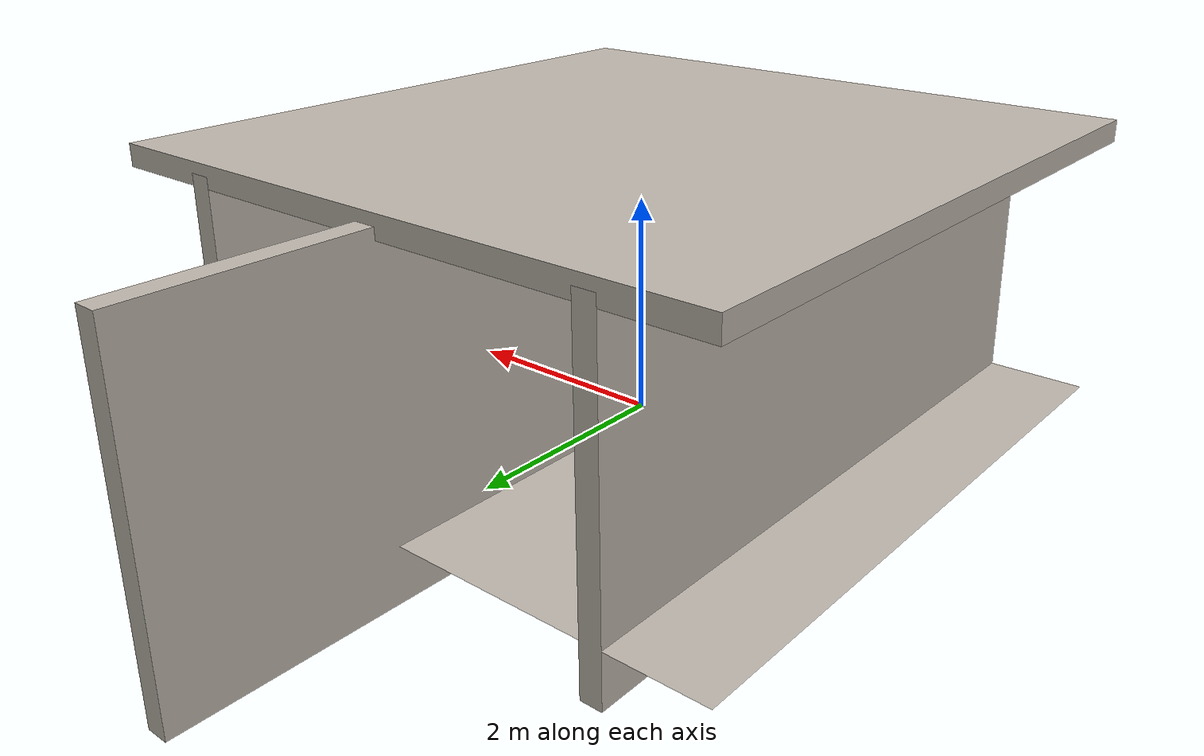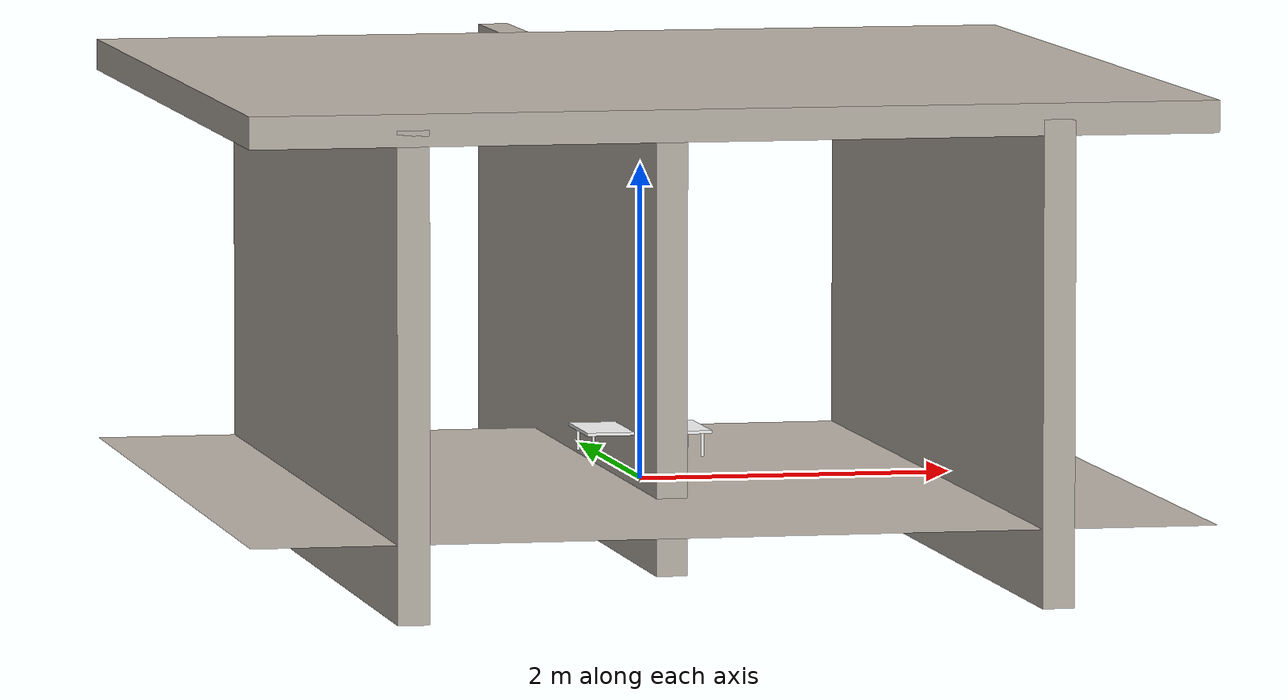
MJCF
<?xml version="1.0" encoding="UTF-8"?>
<mujoco model="piece_bbia">
  <compiler angle="radian" meshdir="../../assets/reachy_official"/>

  <asset>
    <!-- VOS TEXTURES PROCREATE (modifier chemins selon vos fichiers) -->
    <texture name="texture_mur" type="2d" file="../../../assets/textures/mur.png"/>
    <texture name="texture_sol" type="2d" file="../../../assets/textures/sol.png"/>
    <texture name="texture_plafond" type="2d" file="../../../assets/textures/plafond.png"/>

    <!-- Matériaux utilisant vos textures -->
    <material name="mat_mur" texture="texture_mur"/>
    <material name="mat_sol" texture="texture_sol"/>
    <material name="mat_plafond" texture="texture_plafond"/>

    <!-- Skybox BBIA (fond d'environnement) -->
    <texture name="skybox_bbia" type="skybox" builtin="gradient"
             rgb1="0.92 0.92 0.93" rgb2="0.53 0.74 0.98" width="512" height="512"/>
  </asset>

  <worldbody>
    <!-- Sol avec votre texture -->
    <geom name="sol" type="plane" size="3 3 0.1" material="mat_sol" pos="0 0 0"
          contype="1" conaffinity="1"/>

    <!-- Murs de la pièce (4 murs) -->
    <!-- Mur fond (arrière) -->
    <body name="mur_fond" pos="0 2 1">
      <geom type="box" size="0.1 3 1.5" material="mat_mur" contype="0" conaffinity="0"/>
    </body>

    <!-- Mur gauche -->
    <body name="mur_gauche" pos="-2 0 1">
      <geom type="box" size="0.1 3 1.5" material="mat_mur" contype="0" conaffinity="0"/>
    </body>

    <!-- Mur droite -->
    <body name="mur_droite" pos="2 0 1">
      <geom type="box" size="0.1 3 1.5" material="mat_mur" contype="0" conaffinity="0"/>
    </body>

    <!-- Mur avant (devant robot, optionnel avec ouverture) -->
    <!-- Commenté par défaut pour voir le robot -->

    <!-- Plafond -->
    <body name="plafond" pos="0 0 2.5">
      <geom type="box" size="3 3 0.1" material="mat_plafond" contype="0" conaffinity="0"/>
    </body>

    <!-- Bureau blanc (sur lequel repose le robot) -->
    <body name="bureau_bbia" pos="0 0 0.16">
      <geom name="pied_1" type="cylinder" size="0.01 0.075" pos="-0.35 -0.25 0.075"
            rgba="1.0 1.0 1.0 1.0" contype="1" conaffinity="1"/>
      <geom name="pied_2" type="cylinder" size="0.01 0.075" pos="0.35 -0.25 0.075"
            rgba="1.0 1.0 1.0 1.0" contype="1" conaffinity="1"/>
      <geom name="pied_3" type="cylinder" size="0.01 0.075" pos="-0.35 0.25 0.075"
            rgba="1.0 1.0 1.0 1.0" contype="1" conaffinity="1"/>
      <geom name="pied_4" type="cylinder" size="0.01 0.075" pos="0.35 0.25 0.075"
            rgba="1.0 1.0 1.0 1.0" contype="1" conaffinity="1"/>
      <geom name="tabletop" type="box" size="0.4 0.3 0.01" pos="0 0 0.16"
            rgba="1.0 1.0 1.0 1.0" contype="1" conaffinity="1"/>
    </body>

    <!-- Robot Reachy Mini (inclu depuis modèle principal) -->
    <include file="../models/reachy_mini_REAL_OFFICIAL.xml"/>

    <!-- Éclairage -->
    <light pos="0 0 3" dir="0 0 -1" diffuse="0.8 0.8 0.8"/>
    <light pos="2 2 2" dir="-1 -1 -1" diffuse="0.4 0.4 0.4"/>
  </worldbody>
</mujoco>

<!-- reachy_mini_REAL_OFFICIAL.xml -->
<!-- Generated using onshape-to-robot -->
<!-- Onshape https://cad.onshape.com/documents/7836ed39be931c6ece17e007/w/39d557f31a0ba179c9e7bd5b/e/c82436d68c7d00e142abc581 -->
<mujoco model="reachy_mini">
  <compiler angle="radian" meshdir="../assets/reachy_official" autolimits="true"/>
  <default>
    <default class="reachy_mini">
      <joint frictionloss="0.1" armature="0.005"/>
      <position kp="50" dampratio="1"/>
      <default class="visual">
        <geom type="mesh" contype="0" conaffinity="0" group="2"/>
      </default>
      <default class="collision">
        <geom group="3"/>
      </default>
    </default>
  </default>
  <!-- Additional joints_properties.xml -->
  <default>
    <default class="perfect_actuator">
      <geom contype="0" conaffinity="0"/>
      <joint damping="0.095" frictionloss="0.001" armature="0.001"/>
      <position kp="10.0" kv="0.18" forcerange="-10.0 10.0"/>
      <default class="chosen_actuator"/>
    </default>
    <default class="xc330m288t">
      <!-- probably wrong, would need to re-identify -->
      <geom contype="0" conaffinity="0"/>
      <joint damping="0.095" frictionloss="0.058" armature="0.0018"/>
      <position kp="2.54" kv="0.0" forcerange="-0.8 0.8"/>
    </default>
    <default class="sts3215_345">
      <!-- Standard sts3215 with 1/345 gear ratio -->
      <!-- Confident that this is realistic (mini duck walks with these values) -->
      <geom contype="0" conaffinity="0"/>
      <joint damping="0.56" frictionloss="0.068" armature="0.027"/>
      <position kp="17.11" kv="0.0" forcerange="-3.23 3.23"/>
    </default>
    <default class="sts3215_147">
      <!-- sts3215 with 1/147 gear ratio -->
      <!-- (Estimation based on the gear ratio difference) -->
      <geom contype="0" conaffinity="0"/>
      <joint damping="0.1" frictionloss="0.028" armature="0.011"/>
      <position kp="17.11" kv="0.0" forcerange="-1.35 1.35"/>
    </default>
  </default>
  <!-- Additional additional.xml -->
  <contact>
  </contact>
  <default>
    <equality solref="0.002 1" solimp="0.99 0.999 0.0005 0.5 2"/>
  </default>
  <worldbody>
    <!-- Fond BBIA : gris lunaire (#eaeaed) selon brief graphiste -->
    <!-- Palette BBIA : Bleu céleste #87bcfa, Violet #A680FF, Turquoise #60e9e1, Gris lunaire #eaeaed, Rose #FFDAEC -->
    <geom name="background_bbia" type="plane" size="50 50 0.1" pos="0 0 -10" rgba="0.92 0.92 0.93 1" contype="0" conaffinity="0"/>

    <!-- Sol de la pièce (bureau) -->
    <geom name="sol_bureau" type="plane" size="2 2 0.01" pos="0 0 0" rgba="0.85 0.85 0.88 1" contype="1" conaffinity="1"/>

    <!-- Bureau blanc BBIA : le robot repose dessus -->
    <!-- Bureau : 80cm x 60cm, plateau au-dessus des pieds -->
    <body name="bureau_bbia" pos="0 0 0">
      <!-- Support du bureau (4 pieds) : hauteur 0.15m, centre à 0.075m (de 0 à 0.15m) -->
      <geom name="pied_1" type="cylinder" size="0.01 0.075" pos="-0.35 -0.25 0.075" rgba="1.0 1.0 1.0 1.0" contype="1" conaffinity="1"/>
      <geom name="pied_2" type="cylinder" size="0.01 0.075" pos="0.35 -0.25 0.075" rgba="1.0 1.0 1.0 1.0" contype="1" conaffinity="1"/>
      <geom name="pied_3" type="cylinder" size="0.01 0.075" pos="-0.35 0.25 0.075" rgba="1.0 1.0 1.0 1.0" contype="1" conaffinity="1"/>
      <geom name="pied_4" type="cylinder" size="0.01 0.075" pos="0.35 0.25 0.075" rgba="1.0 1.0 1.0 1.0" contype="1" conaffinity="1"/>
      <!-- Plateau du bureau : au-dessus des pieds (centre à 0.16m, épaisseur 0.01m de chaque côté) -->
      <geom name="tabletop" type="box" size="0.4 0.3 0.01" pos="0 0 0.16" rgba="1.0 1.0 1.0 1.0" contype="1" conaffinity="1"/>
    </body>

    <!-- Link body_foot_3dprint -->
    <!-- Robot positionné sur le bureau (hauteur 0.16m pour reposer sur le plateau) -->
    <body name="body_foot_3dprint" pos="0 0 0.16" quat="1 0 0 0" childclass="reachy_mini">
      <inertial pos="0.00290221 0.000112574 0.0132607" mass="0.0617881" fullinertia="6.91521e-05 6.07324e-05 0.000110345 -1.98794e-07 -4.91678e-08 -3.02441e-08"/>
      <!-- Part body_foot_3dprint -->
      <geom type="mesh" class="visual" pos="-2.45997e-07 6.93889e-18 0.2298" quat="0.707107 -2.36704e-18 2.77556e-17 0.707107" mesh="body_foot_3dprint" material="body_foot_3dprint_material"/>
      <!-- Part dc15_a01_horn_dummy -->
      <geom type="mesh" class="visual" pos="-2.45997e-07 6.93889e-18 0.0413" quat="0.5 -0.5 0.5 -0.5" mesh="dc15_a01_horn_dummy" material="dc15_a01_horn_dummy_material"/>
      <!-- Part body_turning_3dprint -->
      <geom type="mesh" class="visual" pos="-2.45997e-07 6.93889e-18 0.2298" quat="0.707107 2.19194e-17 2.29851e-17 0.707107" mesh="body_turning_3dprint" material="body_turning_3dprint_material"/>
      <!-- Link body_down_3dprint -->
      <body name="body_down_3dprint" pos="-2.45997e-07 6.93889e-18 0.0348" quat="0.707107 5.13478e-16 8.88178e-16 -0.707107">
        <!-- Joint from body_foot_3dprint to body_down_3dprint -->
        <joint axis="0 0 1" name="yaw_body" type="hinge" range="-2.792526803190975 2.792526803190879" class="chosen_actuator"/>
        <inertial pos="2.19196e-06 0.000620543 0.0201687" mass="0.78209" fullinertia="0.00233791 0.00224458 0.00254424 1.10376e-07 -1.41892e-07 -4.46122e-05"/>
        <!-- Part body_down_3dprint -->
        <geom type="mesh" class="visual" pos="3.79972e-17 -3.70588e-18 0.195" quat="1.38858e-17 -0 1.67446e-17 1" mesh="body_down_3dprint" material="body_down_3dprint_material"/>
        <!-- Part stewart_tricap_3dprint -->
        <geom type="mesh" class="visual" pos="4.80615e-16 -1.03807e-15 0.195" quat="1.38777e-17 -0 1.67377e-17 1" mesh="stewart_tricap_3dprint" material="stewart_tricap_3dprint_material"/>
        <!-- Part 5w_speaker -->
        <geom type="mesh" class="visual" pos="8.17568e-16 -0.005 0.0535833" quat="9.54336e-15 9.94747e-18 0.707107 0.707107" mesh="5w_speaker" material="5w_speaker_material"/>
        <!-- Part bearing_85x110x13 -->
        <geom type="mesh" class="visual" pos="3.79972e-17 -3.70588e-18 -0.0115" quat="0.5 0.5 0.5 0.5" mesh="bearing_85x110x13" material="bearing_85x110x13_material"/>
        <!-- Part body_top_3dprint -->
        <geom type="mesh" class="visual" pos="6.43558e-16 9.98888e-16 0.195" quat="1.38781e-17 -0 1.67393e-17 1" mesh="body_top_3dprint" material="body_top_3dprint_material"/>
        <!-- Part stewart_main_plate_3dprint -->
        <geom type="mesh" class="visual" pos="-3.07628e-26 -5.29396e-23 0.195" quat="1.38846e-17 0 1.67459e-17 1" mesh="stewart_main_plate_3dprint" material="stewart_main_plate_3dprint_material"/>
        <!-- Part phs_1_7x20_5_dc10_2 -->
        <geom type="mesh" class="visual" pos="-0.01 -0.0501606 0.0418333" quat="8.17339e-16 -1.60549e-14 -1 4.58108e-16" mesh="phs_1_7x20_5_dc10_2" material="phs_1_7x20_5_dc10_2_material"/>
        <!-- Part dc15_a01_case_b_dummy -->
        <geom type="mesh" class="visual" pos="-0.01 -0.0501606 0.0418333" quat="8.17339e-16 -1.60549e-14 -1 4.58108e-16" mesh="dc15_a01_case_b_dummy" material="dc15_a01_case_b_dummy_material"/>
        <!-- Part dc15_a01_case_m_dummy -->
        <geom type="mesh" class="visual" pos="-0.01 -0.0501606 0.0418333" quat="8.17339e-16 -1.60549e-14 -1 4.58108e-16" mesh="dc15_a01_case_m_dummy" material="dc15_a01_case_m_dummy_material"/>
        <!-- Part dc15_a01_led_cap2_dummy -->
        <geom type="mesh" class="visual" pos="-0.01 -0.0501606 0.0418333" quat="8.17339e-16 -1.60549e-14 -1 4.58108e-16" mesh="dc15_a01_led_cap2_dummy" material="dc15_a01_led_cap2_dummy_material"/>
        <!-- Part bts2_m2_6x8 -->
        <geom type="mesh" class="visual" pos="-0.01 -0.0501606 0.0418333" quat="8.17339e-16 -1.60549e-14 -1 4.58108e-16" mesh="bts2_m2_6x8" material="bts2_m2_6x8_material"/>
        <!-- Part dc15_a01_case_f_dummy -->
        <geom type="mesh" class="visual" pos="-0.01 -0.0501606 0.0418333" quat="8.17339e-16 -1.60549e-14 -1 4.58108e-16" mesh="dc15_a01_case_f_dummy" material="dc15_a01_case_f_dummy_material"/>
        <!-- Part b3b_eh_1 -->
        <geom type="mesh" class="visual" pos="-0.01 -0.0501606 0.0418333" quat="8.17339e-16 -1.60549e-14 -1 4.58108e-16" mesh="b3b_eh_1" material="b3b_eh_1_material"/>
        <!-- Part b3b_eh -->
        <geom type="mesh" class="visual" pos="-0.01 -0.0501606 0.0418333" quat="8.17339e-16 -1.60549e-14 -1 4.58108e-16" mesh="b3b_eh" material="b3b_eh_material"/>
        <!-- Part phs_1_7x20_5_dc10_3 -->
        <geom type="mesh" class="visual" pos="-0.01 -0.0501606 0.0418333" quat="8.17339e-16 -1.60549e-14 -1 4.58108e-16" mesh="phs_1_7x20_5_dc10_3" material="phs_1_7x20_5_dc10_3_material"/>
        <!-- Part phs_1_7x20_5_dc10_1 -->
        <geom type="mesh" class="visual" pos="-0.01 -0.0501606 0.0418333" quat="8.17339e-16 -1.60549e-14 -1 4.58108e-16" mesh="phs_1_7x20_5_dc10_1" material="phs_1_7x20_5_dc10_1_material"/>
        <!-- Part phs_1_7x20_5_dc10 -->
        <geom type="mesh" class="visual" pos="-0.01 -0.0501606 0.0418333" quat="8.17339e-16 -1.60549e-14 -1 4.58108e-16" mesh="phs_1_7x20_5_dc10" material="phs_1_7x20_5_dc10_material"/>
        <!-- Part phs_1_7x20_5_dc10_2_2 -->
        <geom type="mesh" class="visual" pos="-0.0384404 0.0337406 0.0418333" quat="8.29278e-16 -0.866025 -0.5 -4.78784e-16" mesh="phs_1_7x20_5_dc10_2" material="phs_1_7x20_5_dc10_2_material"/>
        <!-- Part dc15_a01_case_b_dummy_2 -->
        <geom type="mesh" class="visual" pos="-0.0384404 0.0337406 0.0418333" quat="8.29278e-16 -0.866025 -0.5 -4.78784e-16" mesh="dc15_a01_case_b_dummy" material="dc15_a01_case_b_dummy_material"/>
        <!-- Part dc15_a01_case_m_dummy_2 -->
        <geom type="mesh" class="visual" pos="-0.0384404 0.0337406 0.0418333" quat="8.29278e-16 -0.866025 -0.5 -4.78784e-16" mesh="dc15_a01_case_m_dummy" material="dc15_a01_case_m_dummy_material"/>
        <!-- Part dc15_a01_led_cap2_dummy_2 -->
        <geom type="mesh" class="visual" pos="-0.0384404 0.0337406 0.0418333" quat="8.29278e-16 -0.866025 -0.5 -4.78784e-16" mesh="dc15_a01_led_cap2_dummy" material="dc15_a01_led_cap2_dummy_material"/>
        <!-- Part bts2_m2_6x8_2 -->
        <geom type="mesh" class="visual" pos="-0.0384404 0.0337406 0.0418333" quat="8.29278e-16 -0.866025 -0.5 -4.78784e-16" mesh="bts2_m2_6x8" material="bts2_m2_6x8_material"/>
        <!-- Part dc15_a01_case_f_dummy_2 -->
        <geom type="mesh" class="visual" pos="-0.0384404 0.0337406 0.0418333" quat="8.29278e-16 -0.866025 -0.5 -4.78784e-16" mesh="dc15_a01_case_f_dummy" material="dc15_a01_case_f_dummy_material"/>
        <!-- Part b3b_eh_1_2 -->
        <geom type="mesh" class="visual" pos="-0.0384404 0.0337406 0.0418333" quat="8.29278e-16 -0.866025 -0.5 -4.78784e-16" mesh="b3b_eh_1" material="b3b_eh_1_material"/>
        <!-- Part b3b_eh_2 -->
        <geom type="mesh" class="visual" pos="-0.0384404 0.0337406 0.0418333" quat="8.29278e-16 -0.866025 -0.5 -4.78784e-16" mesh="b3b_eh" material="b3b_eh_material"/>
        <!-- Part phs_1_7x20_5_dc10_3_2 -->
        <geom type="mesh" class="visual" pos="-0.0384404 0.0337406 0.0418333" quat="8.29278e-16 -0.866025 -0.5 -4.78784e-16" mesh="phs_1_7x20_5_dc10_3" material="phs_1_7x20_5_dc10_3_material"/>
        <!-- Part phs_1_7x20_5_dc10_1_2 -->
        <geom type="mesh" class="visual" pos="-0.0384404 0.0337406 0.0418333" quat="8.29278e-16 -0.866025 -0.5 -4.78784e-16" mesh="phs_1_7x20_5_dc10_1" material="phs_1_7x20_5_dc10_1_material"/>
        <!-- Part phs_1_7x20_5_dc10_2 -->
        <geom type="mesh" class="visual" pos="-0.0384404 0.0337406 0.0418333" quat="8.29278e-16 -0.866025 -0.5 -4.78784e-16" mesh="phs_1_7x20_5_dc10" material="phs_1_7x20_5_dc10_material"/>
        <!-- Part phs_1_7x20_5_dc10_2_3 -->
        <geom type="mesh" class="visual" pos="0 -5.29396e-23 0.0065" quat="0.707107 -0.707107 0 -2.3491e-31" mesh="phs_1_7x20_5_dc10_2" material="phs_1_7x20_5_dc10_2_material"/>
        <!-- Part dc15_a01_case_b_dummy_3 -->
        <geom type="mesh" class="visual" pos="0 -5.29396e-23 0.0065" quat="0.707107 -0.707107 0 -2.3491e-31" mesh="dc15_a01_case_b_dummy" material="dc15_a01_case_b_dummy_material"/>
        <!-- Part dc15_a01_case_m_dummy_3 -->
        <geom type="mesh" class="visual" pos="0 -5.29396e-23 0.0065" quat="0.707107 -0.707107 0 -2.3491e-31" mesh="dc15_a01_case_m_dummy" material="dc15_a01_case_m_dummy_material"/>
        <!-- Part dc15_a01_led_cap2_dummy_3 -->
        <geom type="mesh" class="visual" pos="0 -5.29396e-23 0.0065" quat="0.707107 -0.707107 0 -2.3491e-31" mesh="dc15_a01_led_cap2_dummy" material="dc15_a01_led_cap2_dummy_material"/>
        <!-- Part bts2_m2_6x8_3 -->
        <geom type="mesh" class="visual" pos="0 -5.29396e-23 0.0065" quat="0.707107 -0.707107 0 -2.3491e-31" mesh="bts2_m2_6x8" material="bts2_m2_6x8_material"/>
        <!-- Part dc15_a01_case_f_dummy_3 -->
        <geom type="mesh" class="visual" pos="0 -5.29396e-23 0.0065" quat="0.707107 -0.707107 0 -2.3491e-31" mesh="dc15_a01_case_f_dummy" material="dc15_a01_case_f_dummy_material"/>
        <!-- Part b3b_eh_1_3 -->
        <geom type="mesh" class="visual" pos="0 -5.29396e-23 0.0065" quat="0.707107 -0.707107 0 -2.3491e-31" mesh="b3b_eh_1" material="b3b_eh_1_material"/>
        <!-- Part b3b_eh_3 -->
        <geom type="mesh" class="visual" pos="0 -5.29396e-23 0.0065" quat="0.707107 -0.707107 0 -2.3491e-31" mesh="b3b_eh" material="b3b_eh_material"/>
        <!-- Part phs_1_7x20_5_dc10_3_3 -->
        <geom type="mesh" class="visual" pos="0 -5.29396e-23 0.0065" quat="0.707107 -0.707107 0 -2.3491e-31" mesh="phs_1_7x20_5_dc10_3" material="phs_1_7x20_5_dc10_3_material"/>
        <!-- Part phs_1_7x20_5_dc10_1_3 -->
        <geom type="mesh" class="visual" pos="0 -5.29396e-23 0.0065" quat="0.707107 -0.707107 0 -2.3491e-31" mesh="phs_1_7x20_5_dc10_1" material="phs_1_7x20_5_dc10_1_material"/>
        <!-- Part phs_1_7x20_5_dc10_3 -->
        <geom type="mesh" class="visual" pos="0 -5.29396e-23 0.0065" quat="0.707107 -0.707107 0 -2.3491e-31" mesh="phs_1_7x20_5_dc10" material="phs_1_7x20_5_dc10_material"/>
        <!-- Part phs_1_7x20_5_dc10_2_4 -->
        <geom type="mesh" class="visual" pos="0.0384404 0.0337406 0.0418333" quat="8.29278e-16 -0.866025 0.5 4.78784e-16" mesh="phs_1_7x20_5_dc10_2" material="phs_1_7x20_5_dc10_2_material"/>
        <!-- Part dc15_a01_case_b_dummy_4 -->
        <geom type="mesh" class="visual" pos="0.0384404 0.0337406 0.0418333" quat="8.29278e-16 -0.866025 0.5 4.78784e-16" mesh="dc15_a01_case_b_dummy" material="dc15_a01_case_b_dummy_material"/>
        <!-- Part dc15_a01_case_m_dummy_4 -->
        <geom type="mesh" class="visual" pos="0.0384404 0.0337406 0.0418333" quat="8.29278e-16 -0.866025 0.5 4.78784e-16" mesh="dc15_a01_case_m_dummy" material="dc15_a01_case_m_dummy_material"/>
        <!-- Part dc15_a01_led_cap2_dummy_4 -->
        <geom type="mesh" class="visual" pos="0.0384404 0.0337406 0.0418333" quat="8.29278e-16 -0.866025 0.5 4.78784e-16" mesh="dc15_a01_led_cap2_dummy" material="dc15_a01_led_cap2_dummy_material"/>
        <!-- Part bts2_m2_6x8_4 -->
        <geom type="mesh" class="visual" pos="0.0384404 0.0337406 0.0418333" quat="8.29278e-16 -0.866025 0.5 4.78784e-16" mesh="bts2_m2_6x8" material="bts2_m2_6x8_material"/>
        <!-- Part dc15_a01_case_f_dummy_4 -->
        <geom type="mesh" class="visual" pos="0.0384404 0.0337406 0.0418333" quat="8.29278e-16 -0.866025 0.5 4.78784e-16" mesh="dc15_a01_case_f_dummy" material="dc15_a01_case_f_dummy_material"/>
        <!-- Part b3b_eh_1_4 -->
        <geom type="mesh" class="visual" pos="0.0384404 0.0337406 0.0418333" quat="8.29278e-16 -0.866025 0.5 4.78784e-16" mesh="b3b_eh_1" material="b3b_eh_1_material"/>
        <!-- Part b3b_eh_4 -->
        <geom type="mesh" class="visual" pos="0.0384404 0.0337406 0.0418333" quat="8.29278e-16 -0.866025 0.5 4.78784e-16" mesh="b3b_eh" material="b3b_eh_material"/>
        <!-- Part phs_1_7x20_5_dc10_3_4 -->
        <geom type="mesh" class="visual" pos="0.0384404 0.0337406 0.0418333" quat="8.29278e-16 -0.866025 0.5 4.78784e-16" mesh="phs_1_7x20_5_dc10_3" material="phs_1_7x20_5_dc10_3_material"/>
        <!-- Part phs_1_7x20_5_dc10_1_4 -->
        <geom type="mesh" class="visual" pos="0.0384404 0.0337406 0.0418333" quat="8.29278e-16 -0.866025 0.5 4.78784e-16" mesh="phs_1_7x20_5_dc10_1" material="phs_1_7x20_5_dc10_1_material"/>
        <!-- Part phs_1_7x20_5_dc10_4 -->
        <geom type="mesh" class="visual" pos="0.0384404 0.0337406 0.0418333" quat="8.29278e-16 -0.866025 0.5 4.78784e-16" mesh="phs_1_7x20_5_dc10" material="phs_1_7x20_5_dc10_material"/>
        <!-- Part phs_1_7x20_5_dc10_2_5 -->
        <geom type="mesh" class="visual" pos="0.01 -0.0501606 0.0418333" quat="8.17116e-16 -1.6695e-14 1 -4.57765e-16" mesh="phs_1_7x20_5_dc10_2" material="phs_1_7x20_5_dc10_2_material"/>
        <!-- Part dc15_a01_case_b_dummy_5 -->
        <geom type="mesh" class="visual" pos="0.01 -0.0501606 0.0418333" quat="8.17116e-16 -1.6695e-14 1 -4.57765e-16" mesh="dc15_a01_case_b_dummy" material="dc15_a01_case_b_dummy_material"/>
        <!-- Part dc15_a01_case_m_dummy_5 -->
        <geom type="mesh" class="visual" pos="0.01 -0.0501606 0.0418333" quat="8.17116e-16 -1.6695e-14 1 -4.57765e-16" mesh="dc15_a01_case_m_dummy" material="dc15_a01_case_m_dummy_material"/>
        <!-- Part dc15_a01_led_cap2_dummy_5 -->
        <geom type="mesh" class="visual" pos="0.01 -0.0501606 0.0418333" quat="8.17116e-16 -1.6695e-14 1 -4.57765e-16" mesh="dc15_a01_led_cap2_dummy" material="dc15_a01_led_cap2_dummy_material"/>
        <!-- Part bts2_m2_6x8_5 -->
        <geom type="mesh" class="visual" pos="0.01 -0.0501606 0.0418333" quat="8.17116e-16 -1.6695e-14 1 -4.57765e-16" mesh="bts2_m2_6x8" material="bts2_m2_6x8_material"/>
        <!-- Part dc15_a01_case_f_dummy_5 -->
        <geom type="mesh" class="visual" pos="0.01 -0.0501606 0.0418333" quat="8.17116e-16 -1.6695e-14 1 -4.57765e-16" mesh="dc15_a01_case_f_dummy" material="dc15_a01_case_f_dummy_material"/>
        <!-- Part b3b_eh_1_5 -->
        <geom type="mesh" class="visual" pos="0.01 -0.0501606 0.0418333" quat="8.17116e-16 -1.6695e-14 1 -4.57765e-16" mesh="b3b_eh_1" material="b3b_eh_1_material"/>
        <!-- Part b3b_eh_5 -->
        <geom type="mesh" class="visual" pos="0.01 -0.0501606 0.0418333" quat="8.17116e-16 -1.6695e-14 1 -4.57765e-16" mesh="b3b_eh" material="b3b_eh_material"/>
        <!-- Part phs_1_7x20_5_dc10_3_5 -->
        <geom type="mesh" class="visual" pos="0.01 -0.0501606 0.0418333" quat="8.17116e-16 -1.6695e-14 1 -4.57765e-16" mesh="phs_1_7x20_5_dc10_3" material="phs_1_7x20_5_dc10_3_material"/>
        <!-- Part phs_1_7x20_5_dc10_1_5 -->
        <geom type="mesh" class="visual" pos="0.01 -0.0501606 0.0418333" quat="8.17116e-16 -1.6695e-14 1 -4.57765e-16" mesh="phs_1_7x20_5_dc10_1" material="phs_1_7x20_5_dc10_1_material"/>
        <!-- Part phs_1_7x20_5_dc10_5 -->
        <geom type="mesh" class="visual" pos="0.01 -0.0501606 0.0418333" quat="8.17116e-16 -1.6695e-14 1 -4.57765e-16" mesh="phs_1_7x20_5_dc10" material="phs_1_7x20_5_dc10_material"/>
        <!-- Part phs_1_7x20_5_dc10_2_6 -->
        <geom type="mesh" class="visual" pos="-0.0484404 0.01642 0.0418333" quat="1.20185e-17 -0.866025 -0.5 9.36751e-16" mesh="phs_1_7x20_5_dc10_2" material="phs_1_7x20_5_dc10_2_material"/>
        <!-- Part dc15_a01_case_b_dummy_6 -->
        <geom type="mesh" class="visual" pos="-0.0484404 0.01642 0.0418333" quat="1.20185e-17 -0.866025 -0.5 9.36751e-16" mesh="dc15_a01_case_b_dummy" material="dc15_a01_case_b_dummy_material"/>
        <!-- Part dc15_a01_case_m_dummy_6 -->
        <geom type="mesh" class="visual" pos="-0.0484404 0.01642 0.0418333" quat="1.20185e-17 -0.866025 -0.5 9.36751e-16" mesh="dc15_a01_case_m_dummy" material="dc15_a01_case_m_dummy_material"/>
        <!-- Part dc15_a01_led_cap2_dummy_6 -->
        <geom type="mesh" class="visual" pos="-0.0484404 0.01642 0.0418333" quat="1.20185e-17 -0.866025 -0.5 9.36751e-16" mesh="dc15_a01_led_cap2_dummy" material="dc15_a01_led_cap2_dummy_material"/>
        <!-- Part bts2_m2_6x8_6 -->
        <geom type="mesh" class="visual" pos="-0.0484404 0.01642 0.0418333" quat="1.20185e-17 -0.866025 -0.5 9.36751e-16" mesh="bts2_m2_6x8" material="bts2_m2_6x8_material"/>
        <!-- Part dc15_a01_case_f_dummy_6 -->
        <geom type="mesh" class="visual" pos="-0.0484404 0.01642 0.0418333" quat="1.20185e-17 -0.866025 -0.5 9.36751e-16" mesh="dc15_a01_case_f_dummy" material="dc15_a01_case_f_dummy_material"/>
        <!-- Part b3b_eh_1_6 -->
        <geom type="mesh" class="visual" pos="-0.0484404 0.01642 0.0418333" quat="1.20185e-17 -0.866025 -0.5 9.36751e-16" mesh="b3b_eh_1" material="b3b_eh_1_material"/>
        <!-- Part b3b_eh_6 -->
        <geom type="mesh" class="visual" pos="-0.0484404 0.01642 0.0418333" quat="1.20185e-17 -0.866025 -0.5 9.36751e-16" mesh="b3b_eh" material="b3b_eh_material"/>
        <!-- Part phs_1_7x20_5_dc10_3_6 -->
        <geom type="mesh" class="visual" pos="-0.0484404 0.01642 0.0418333" quat="1.20185e-17 -0.866025 -0.5 9.36751e-16" mesh="phs_1_7x20_5_dc10_3" material="phs_1_7x20_5_dc10_3_material"/>
        <!-- Part phs_1_7x20_5_dc10_1_6 -->
        <geom type="mesh" class="visual" pos="-0.0484404 0.01642 0.0418333" quat="1.20185e-17 -0.866025 -0.5 9.36751e-16" mesh="phs_1_7x20_5_dc10_1" material="phs_1_7x20_5_dc10_1_material"/>
        <!-- Part phs_1_7x20_5_dc10_6 -->
        <geom type="mesh" class="visual" pos="-0.0484404 0.01642 0.0418333" quat="1.20185e-17 -0.866025 -0.5 9.36751e-16" mesh="phs_1_7x20_5_dc10" material="phs_1_7x20_5_dc10_material"/>
        <!-- Part phs_1_7x20_5_dc10_2_7 -->
        <geom type="mesh" class="visual" pos="0.0484404 0.01642 0.0418333" quat="1.20185e-17 -0.866025 0.5 -9.36751e-16" mesh="phs_1_7x20_5_dc10_2" material="phs_1_7x20_5_dc10_2_material"/>
        <!-- Part dc15_a01_case_b_dummy_7 -->
        <geom type="mesh" class="visual" pos="0.0484404 0.01642 0.0418333" quat="1.20185e-17 -0.866025 0.5 -9.36751e-16" mesh="dc15_a01_case_b_dummy" material="dc15_a01_case_b_dummy_material"/>
        <!-- Part dc15_a01_case_m_dummy_7 -->
        <geom type="mesh" class="visual" pos="0.0484404 0.01642 0.0418333" quat="1.20185e-17 -0.866025 0.5 -9.36751e-16" mesh="dc15_a01_case_m_dummy" material="dc15_a01_case_m_dummy_material"/>
        <!-- Part dc15_a01_led_cap2_dummy_7 -->
        <geom type="mesh" class="visual" pos="0.0484404 0.01642 0.0418333" quat="1.20185e-17 -0.866025 0.5 -9.36751e-16" mesh="dc15_a01_led_cap2_dummy" material="dc15_a01_led_cap2_dummy_material"/>
        <!-- Part bts2_m2_6x8_7 -->
        <geom type="mesh" class="visual" pos="0.0484404 0.01642 0.0418333" quat="1.20185e-17 -0.866025 0.5 -9.36751e-16" mesh="bts2_m2_6x8" material="bts2_m2_6x8_material"/>
        <!-- Part dc15_a01_case_f_dummy_7 -->
        <geom type="mesh" class="visual" pos="0.0484404 0.01642 0.0418333" quat="1.20185e-17 -0.866025 0.5 -9.36751e-16" mesh="dc15_a01_case_f_dummy" material="dc15_a01_case_f_dummy_material"/>
        <!-- Part b3b_eh_1_7 -->
        <geom type="mesh" class="visual" pos="0.0484404 0.01642 0.0418333" quat="1.20185e-17 -0.866025 0.5 -9.36751e-16" mesh="b3b_eh_1" material="b3b_eh_1_material"/>
        <!-- Part b3b_eh_7 -->
        <geom type="mesh" class="visual" pos="0.0484404 0.01642 0.0418333" quat="1.20185e-17 -0.866025 0.5 -9.36751e-16" mesh="b3b_eh" material="b3b_eh_material"/>
        <!-- Part phs_1_7x20_5_dc10_3_7 -->
        <geom type="mesh" class="visual" pos="0.0484404 0.01642 0.0418333" quat="1.20185e-17 -0.866025 0.5 -9.36751e-16" mesh="phs_1_7x20_5_dc10_3" material="phs_1_7x20_5_dc10_3_material"/>
        <!-- Part phs_1_7x20_5_dc10_1_7 -->
        <geom type="mesh" class="visual" pos="0.0484404 0.01642 0.0418333" quat="1.20185e-17 -0.866025 0.5 -9.36751e-16" mesh="phs_1_7x20_5_dc10_1" material="phs_1_7x20_5_dc10_1_material"/>
        <!-- Part phs_1_7x20_5_dc10_7 -->
        <geom type="mesh" class="visual" pos="0.0484404 0.01642 0.0418333" quat="1.20185e-17 -0.866025 0.5 -9.36751e-16" mesh="phs_1_7x20_5_dc10" material="phs_1_7x20_5_dc10_material"/>
        <!-- Link dc15_a01_horn_dummy -->
        <body name="dc15_a01_horn_dummy" pos="-0.0328112 0.0304906 0.0418333" quat="0.612372 0.612372 0.353553 0.353553">
          <!-- Joint from body_down_3dprint to dc15_a01_horn_dummy -->
          <joint axis="0 0 1" name="stewart_1" type="hinge" range="-0.8377580409572196 1.3962634015955222" class="chosen_actuator"/>
          <inertial pos="0.0237505 1.13786e-09 0.00335838" mass="0.00366675" fullinertia="8.57063e-08 1.28019e-06 1.26546e-06 1.81822e-13 -1.93125e-07 1.09002e-14"/>
          <!-- Part dc15_a01_horn_dummy_2 -->
          <geom type="mesh" class="visual" pos="3.46945e-18 0 -0.0065" quat="0.5 0.5 -0.5 -0.5" mesh="dc15_a01_horn_dummy" material="dc15_a01_horn_dummy_material"/>
          <!-- Part mp01062_stewart_arm_3 -->
          <geom type="mesh" class="visual" pos="-0.01 -0.153167 0.0436606" quat="0.612372 0.612372 -0.353553 0.353553" mesh="mp01062_stewart_arm_3" material="mp01062_stewart_arm_3_material"/>
          <!-- Part stewart_link_ball -->
          <geom type="mesh" class="visual" pos="0.0825 -1.6545e-10 0.007" quat="1 1.09495e-14 1.77636e-15 2.19524e-15" mesh="stewart_link_ball" material="stewart_link_ball_material"/>
          <!-- Link stewart_link_rod -->
          <body name="stewart_link_rod" pos="0.04 -1.6545e-10 0.007" quat="0.497033 0.00414178 -0.0814283 0.863893">
            <!-- Joint from dc15_a01_horn_dummy to stewart_link_rod -->
            <joint axis="0 0 1" name="passive_1" type="ball" class="chosen_actuator"/>
            <inertial pos="0.0425001 8.43768e-11 -1.88428e-09" mass="0.00503424" fullinertia="2.63976e-08 3.65211e-06 3.66473e-06 -3.69517e-13 7.12534e-14 5.21041e-14"/>
            <!-- Part stewart_link_rod -->
            <geom type="mesh" class="visual" pos="0.0425 0 6.93889e-18" quat="1 -6.66292e-18 5.55112e-17 1.31391e-16" mesh="stewart_link_rod" material="stewart_link_rod_material"/>
            <!-- Frame closing_1_1 -->
            <site group="3" name="closing_1_1" pos="0.085 -1.38778e-17 0" quat="1 -6.66292e-18 5.55112e-17 1.31391e-16"/>
          </body>
        </body>
        <!-- Link dc15_a01_horn_dummy_2 -->
        <body name="dc15_a01_horn_dummy_2" pos="-0.0428112 0.01317 0.0418333" quat="0.353553 -0.353553 0.612372 -0.612372">
          <!-- Joint from body_down_3dprint to dc15_a01_horn_dummy_2 -->
          <joint axis="0 0 1" name="stewart_2" type="hinge" range="-1.396263401595614 1.2217304763958803" class="chosen_actuator"/>
          <inertial pos="0.0237505 1.27591e-09 0.00335838" mass="0.00366675" fullinertia="8.57063e-08 1.28019e-06 1.26546e-06 1.79436e-13 -1.93125e-07 1.03818e-14"/>
          <!-- Part stewart_link_ball_2 -->
          <geom type="mesh" class="visual" pos="-0.0025 4.16334e-17 0.007" quat="6.30546e-15 -6.04913e-15 1.19904e-14 1" mesh="stewart_link_ball" material="stewart_link_ball_material"/>
          <!-- Part dc15_a01_horn_dummy_3 -->
          <geom type="mesh" class="visual" pos="-1.73472e-18 0 -0.0065" quat="0.5 0.5 -0.5 -0.5" mesh="dc15_a01_horn_dummy" material="dc15_a01_horn_dummy_material"/>
          <!-- Part mp01062_stewart_arm_3_2 -->
          <geom type="mesh" class="visual" pos="-0.01 -0.153167 0.0436606" quat="0.612372 0.612372 -0.353553 0.353553" mesh="mp01062_stewart_arm_3" material="mp01062_stewart_arm_3_material"/>
          <!-- Link stewart_link_rod_2 -->
          <body name="stewart_link_rod_2" pos="0.04 1.249e-16 0.007" quat="6.10896e-15 6.31057e-15 1 -1.23174e-14">
            <!-- Joint from dc15_a01_horn_dummy_2 to stewart_link_rod_2 -->
            <joint axis="0 0 1" name="passive_2" type="ball" class="chosen_actuator"/>
            <inertial pos="0.0214999 -0.0364688 -0.00374429" mass="0.00503424" fullinertia="2.72424e-06 9.82586e-07 3.63642e-06 1.57393e-06 1.6134e-07 -2.75528e-07"/>
            <!-- Part stewart_link_rod_2 -->
            <geom type="mesh" class="visual" pos="0.0215 -0.0364689 -0.0037443" quat="0.0195742 -0.496665 -0.866005 -0.0545625" mesh="stewart_link_rod" material="stewart_link_rod_material"/>
            <!-- Frame closing_2_1 -->
            <site group="3" name="closing_2_1" pos="0.043 -0.0729378 -0.00748861" quat="0.0195742 -0.496665 -0.866005 -0.0545625"/>
          </body>
        </body>
        <!-- Link dc15_a01_horn_dummy_3 -->
        <body name="dc15_a01_horn_dummy_3" pos="-0.01 -0.0436606 0.0418333" quat="3.19818e-14 -5.957e-15 0.707107 0.707107">
          <!-- Joint from body_down_3dprint to dc15_a01_horn_dummy_3 -->
          <joint axis="0 0 1" name="stewart_3" type="hinge" range="-0.8377580409572173 1.3962634015955244" class="chosen_actuator"/>
          <inertial pos="0.0237505 1.27591e-09 0.00335838" mass="0.00366675" fullinertia="8.57063e-08 1.28019e-06 1.26546e-06 1.79436e-13 -1.93125e-07 1.03818e-14"/>
          <!-- Part dc15_a01_horn_dummy_4 -->
          <geom type="mesh" class="visual" pos="-1.73472e-18 1.38778e-17 -0.0065" quat="0.5 0.5 -0.5 -0.5" mesh="dc15_a01_horn_dummy" material="dc15_a01_horn_dummy_material"/>
          <!-- Part stewart_link_ball_3 -->
          <geom type="mesh" class="visual" pos="0.04 -0.0425 0.007" quat="0.707107 -4.06341e-15 -6.43929e-15 -0.707107" mesh="stewart_link_ball" material="stewart_link_ball_material"/>
          <!-- Part mp01062_stewart_arm_3_3 -->
          <geom type="mesh" class="visual" pos="-0.01 -0.153167 0.0436606" quat="0.612372 0.612372 -0.353553 0.353553" mesh="mp01062_stewart_arm_3" material="mp01062_stewart_arm_3_material"/>
          <!-- Link stewart_link_rod_3 -->
          <body name="stewart_link_rod_3" pos="0.04 8.32667e-17 0.007" quat="0.848296 0.182577 -0.0544081 -0.494063">
            <!-- Joint from dc15_a01_horn_dummy_3 to stewart_link_rod_3 -->
            <joint axis="0 0 1" name="passive_3" type="ball" class="chosen_actuator"/>
            <inertial pos="-0.0424999 8.43768e-11 -1.88428e-09" mass="0.00503424" fullinertia="2.63976e-08 3.65211e-06 3.66473e-06 -3.69517e-13 7.12534e-14 5.21041e-14"/>
            <!-- Part stewart_link_rod_3 -->
            <geom type="mesh" class="visual" pos="-0.0425 -1.38778e-17 0" quat="1 0 2.22045e-16 5.35987e-17" mesh="stewart_link_rod" material="stewart_link_rod_material"/>
            <!-- Frame closing_3_1 -->
            <site group="3" name="closing_3_1" pos="-0.085 -1.38778e-17 0" quat="1 0 2.22045e-16 5.35987e-17"/>
          </body>
        </body>
        <!-- Link dc15_a01_horn_dummy_4 -->
        <body name="dc15_a01_horn_dummy_4" pos="0.01 -0.0436606 0.0418333" quat="0.707107 -0.707107 -3.64153e-14 -1.2529e-14">
          <!-- Joint from body_down_3dprint to dc15_a01_horn_dummy_4 -->
          <joint axis="0 0 1" name="stewart_4" type="hinge" range="-1.3962634015953894 0.8377580409573525" class="chosen_actuator"/>
          <inertial pos="0.0237505 1.27591e-09 0.00335838" mass="0.00366675" fullinertia="8.57063e-08 1.28019e-06 1.26546e-06 1.79436e-13 -1.93125e-07 1.03818e-14"/>
          <!-- Part stewart_link_ball_4 -->
          <geom type="mesh" class="visual" pos="0.04 0.0425 0.007" quat="0.707107 -6.93925e-16 -0 0.707107" mesh="stewart_link_ball" material="stewart_link_ball_material"/>
          <!-- Part mp01062_stewart_arm_3_4 -->
          <geom type="mesh" class="visual" pos="-0.01 -0.153167 0.0436606" quat="0.612372 0.612372 -0.353553 0.353553" mesh="mp01062_stewart_arm_3" material="mp01062_stewart_arm_3_material"/>
          <!-- Part dc15_a01_horn_dummy_5 -->
          <geom type="mesh" class="visual" pos="-1.73472e-18 -1.38778e-17 -0.0065" quat="0.5 0.5 -0.5 -0.5" mesh="dc15_a01_horn_dummy" material="dc15_a01_horn_dummy_material"/>
          <!-- Link stewart_link_rod_4 -->
          <body name="stewart_link_rod_4" pos="0.04 2.77556e-17 0.007" quat="0.865702 -0.0591779 0.0169265 0.496762">
            <!-- Joint from dc15_a01_horn_dummy_4 to stewart_link_rod_4 -->
            <joint axis="0 0 1" name="passive_4" type="ball" class="chosen_actuator"/>
            <inertial pos="-0.0424999 8.43769e-11 -1.88428e-09" mass="0.00503424" fullinertia="2.63976e-08 3.65211e-06 3.66473e-06 -3.69517e-13 7.12534e-14 5.21041e-14"/>
            <!-- Part stewart_link_rod_4 -->
            <geom type="mesh" class="visual" pos="-0.0425 1.38778e-17 0" quat="1 0 5.55112e-17 -1.17998e-16" mesh="stewart_link_rod" material="stewart_link_rod_material"/>
            <!-- Frame closing_4_1 -->
            <site group="3" name="closing_4_1" pos="-0.085 2.77556e-17 0" quat="1 0 5.55112e-17 -1.17998e-16"/>
          </body>
        </body>
        <!-- Link dc15_a01_horn_dummy_5 -->
        <body name="dc15_a01_horn_dummy_5" pos="0.0428112 0.01317 0.0418333" quat="0.612372 0.612372 -0.353553 -0.353553">
          <!-- Joint from body_down_3dprint to dc15_a01_horn_dummy_5 -->
          <joint axis="0 0 1" name="stewart_5" type="hinge" range="-1.2217304763962082 1.396263401595286" class="chosen_actuator"/>
          <inertial pos="0.0237505 1.27591e-09 0.00335838" mass="0.00366675" fullinertia="8.57063e-08 1.28019e-06 1.26546e-06 1.79436e-13 -1.93125e-07 1.03818e-14"/>
          <!-- Part mp01062_stewart_arm_3_5 -->
          <geom type="mesh" class="visual" pos="-0.01 -0.153167 0.0436606" quat="0.612372 0.612372 -0.353553 0.353553" mesh="mp01062_stewart_arm_3" material="mp01062_stewart_arm_3_material"/>
          <!-- Part stewart_link_ball_5 -->
          <geom type="mesh" class="visual" pos="-0.0025 8.32667e-17 0.007" quat="1.02062e-16 6.9016e-15 -4.44089e-16 -1" mesh="stewart_link_ball" material="stewart_link_ball_material"/>
          <!-- Part dc15_a01_horn_dummy_6 -->
          <geom type="mesh" class="visual" pos="0 0 -0.0065" quat="0.5 0.5 -0.5 -0.5" mesh="dc15_a01_horn_dummy" material="dc15_a01_horn_dummy_material"/>
          <!-- Link stewart_link_rod_5 -->
          <body name="stewart_link_rod_5" pos="0.04 5.55112e-17 0.007" quat="0.864425 0.0755679 0.00751236 -0.496993">
            <!-- Joint from dc15_a01_horn_dummy_5 to stewart_link_rod_5 -->
            <joint axis="0 0 1" name="passive_5" type="ball" class="chosen_actuator"/>
            <inertial pos="-0.0424999 8.43768e-11 -1.88428e-09" mass="0.00503424" fullinertia="2.63976e-08 3.65211e-06 3.66473e-06 -3.69517e-13 7.12534e-14 5.21041e-14"/>
            <!-- Part stewart_link_rod_5 -->
            <geom type="mesh" class="visual" pos="-0.0425 0 0" quat="1 0 1.11022e-16 2.31852e-16" mesh="stewart_link_rod" material="stewart_link_rod_material"/>
            <!-- Frame closing_5_1 -->
            <site group="3" name="closing_5_1" pos="-0.085 -1.38778e-17 0" quat="1 0 1.11022e-16 2.31852e-16"/>
          </body>
        </body>
        <!-- Link dc15_a01_horn_dummy_6 -->
        <body name="dc15_a01_horn_dummy_6" pos="0.0328112 0.0304906 0.0418333" quat="0.353553 -0.353553 -0.612372 0.612372">
          <!-- Joint from body_down_3dprint to dc15_a01_horn_dummy_6 -->
          <joint axis="0 0 1" name="stewart_6" type="hinge" range="-1.3962634015954123 0.8377580409573296" class="chosen_actuator"/>
          <inertial pos="0.0237505 1.27591e-09 0.00335838" mass="0.00366675" fullinertia="8.57063e-08 1.28019e-06 1.26546e-06 1.79436e-13 -1.93125e-07 1.03818e-14"/>
          <!-- Part dc15_a01_horn_dummy_7 -->
          <geom type="mesh" class="visual" pos="3.46945e-18 0 -0.0065" quat="0.5 0.5 -0.5 -0.5" mesh="dc15_a01_horn_dummy" material="dc15_a01_horn_dummy_material"/>
          <!-- Part stewart_link_ball_6 -->
          <geom type="mesh" class="visual" pos="0.0825 8.32667e-17 0.007" quat="1 6.26127e-15 7.27196e-15 1.9618e-14" mesh="stewart_link_ball" material="stewart_link_ball_material"/>
          <!-- Part mp01062_stewart_arm_3_6 -->
          <geom type="mesh" class="visual" pos="-0.01 -0.153167 0.0436606" quat="0.612372 0.612372 -0.353553 0.353553" mesh="mp01062_stewart_arm_3" material="mp01062_stewart_arm_3_material"/>
          <!-- Link stewart_link_rod_6 -->
          <body name="stewart_link_rod_6" pos="0.04 9.71445e-17 0.007" quat="0.0566689 0.865869 0.496711 -0.018366">
            <!-- Joint from dc15_a01_horn_dummy_6 to stewart_link_rod_6 -->
            <joint axis="0 0 1" name="passive_6" type="ball" class="chosen_actuator"/>
            <inertial pos="-0.0424999 8.43768e-11 -1.88428e-09" mass="0.00503424" fullinertia="2.63976e-08 3.65211e-06 3.66473e-06 -3.69517e-13 7.12534e-14 5.21041e-14"/>
            <!-- Part stewart_link_rod_6 -->
            <geom type="mesh" class="visual" pos="-0.0425 0 0" quat="1 0 -1.11022e-16 5.66481e-17" mesh="stewart_link_rod" material="stewart_link_rod_material"/>
            <!-- Link xl_330 -->
            <body name="xl_330" pos="-0.085 0 0" quat="0 1 0 0">
              <!-- Joint from stewart_link_rod_6 to xl_330 -->
              <joint axis="0 0 1" name="passive_7" type="ball" class="chosen_actuator"/>
              <inertial pos="-0.0487051 -0.0237648 0.020658" mass="0.259259" fullinertia="0.000634651 0.000587786 0.000460283 3.65691e-05 -2.18087e-05 9.29467e-05"/>
              <!-- Part m12_fisheye_lens_1_8mm -->
              <geom type="mesh" class="visual" pos="-0.0387195 -0.0329451 -0.0240431" quat="0.182968 0.474809 0.465151 0.724371" mesh="m12_fisheye_lens_1_8mm" material="m12_fisheye_lens_1_8mm_material"/>
              <!-- Part stewart_link_ball_7 -->
              <geom type="mesh" class="visual" pos="0.0175286 0.0420772 0.0551172" quat="0.176467 -0.199534 0.847949 -0.458289" mesh="stewart_link_ball__2" material="stewart_link_ball__2_material"/>
              <!-- Part big_lens_d40 -->
              <geom type="mesh" class="visual" pos="-0.0262968 -0.0511554 -0.0373805" quat="0.182968 0.474809 0.465151 0.724371" mesh="big_lens_d40" material="big_lens_d40_material"/>
              <!-- Part neck_reference_3dprint -->
              <geom type="mesh" class="visual" pos="-0.0535717 -0.0190178 0.0256147" quat="0.664652 0.38283 -0.641585 -0.00682952" mesh="neck_reference_3dprint" material="neck_reference_3dprint_material"/>
              <!-- Part head_back_3dprint -->
              <geom type="mesh" class="visual" pos="-0.0535717 -0.0190178 0.0256147" quat="0.664652 0.38283 -0.641585 -0.00682952" mesh="head_back_3dprint" material="head_back_3dprint_material"/>
              <!-- Part arducam -->
              <geom type="mesh" class="visual" pos="-0.045905 -0.0448628 -0.0036254" quat="0.00682952 -0.641585 -0.38283 0.664652" mesh="arducam" material="arducam_material"/>
              <!-- Part pp01102_arducam_carter -->
              <geom type="mesh" class="visual" pos="-0.0311515 -0.0518836 0.00154345" quat="0.664652 0.38283 -0.641585 -0.00682952" mesh="pp01102_arducam_carter" material="pp01102_arducam_carter_material"/>
              <!-- Part antenna_holder_l_3dprint -->
              <geom type="mesh" class="visual" pos="-0.0536682 -0.0188765 0.0257182" quat="0.664652 0.38283 -0.641585 -0.00682952" mesh="antenna_holder_l_3dprint" material="antenna_holder_l_3dprint_material"/>
              <!-- Part stewart_link_ball_8 -->
              <geom type="mesh" class="visual" pos="-0.00630385 -0.00639493 0.0739606" quat="0.297432 -0.759048 0.40183 0.417029" mesh="stewart_link_ball__2" material="stewart_link_ball__2_material"/>
              <!-- Part lens_cap_d30_3dprint -->
              <geom type="mesh" class="visual" pos="-0.0536562 -0.018894 0.0257054" quat="0.664652 0.38283 -0.641585 -0.00682952" mesh="lens_cap_d30_3dprint" material="lens_cap_d30_3dprint_material"/>
              <!-- Part lens_cap_d40_3dprint -->
              <geom type="mesh" class="visual" pos="-0.0536391 -0.0189191 0.025687" quat="0.664652 0.38283 -0.641585 -0.00682952" mesh="lens_cap_d40_3dprint" material="lens_cap_d40_3dprint_material"/>
              <!-- Part antenna_holder_r_3dprint -->
              <geom type="mesh" class="visual" pos="-0.0536682 -0.0188765 0.0257182" quat="0.664652 0.38283 -0.641585 -0.00682952" mesh="antenna_holder_r_3dprint" material="antenna_holder_r_3dprint_material"/>
              <!-- Part stewart_link_ball_9 -->
              <geom type="mesh" class="visual" pos="0.0150556 0.0490816 0.0432504" quat="0.176467 -0.199534 0.847949 -0.458289" mesh="stewart_link_ball__2" material="stewart_link_ball__2_material"/>
              <!-- Part small_lens_d30 -->
              <geom type="mesh" class="visual" pos="-0.0244054 -0.0696173 0.0280123" quat="0.182968 0.474809 0.465151 0.724371" mesh="small_lens_d30" material="small_lens_d30_material"/>
              <!-- Part stewart_link_ball_10 -->
              <geom type="mesh" class="visual" pos="-0.0109132 -0.00132777 0.0861703" quat="0.297432 -0.759048 0.40183 0.417029" mesh="stewart_link_ball__2" material="stewart_link_ball__2_material"/>
              <!-- Part stewart_link_ball_11 -->
              <geom type="mesh" class="visual" pos="-0.0215 0.0366458 0.00104087" quat="0.865869 0.0566689 -0.018366 -0.496711" mesh="stewart_link_ball__2" material="stewart_link_ball__2_material"/>
              <!-- Part glasses_dolder_3dprint -->
              <geom type="mesh" class="visual" pos="-0.0535717 -0.0190178 0.0256147" quat="0.664652 0.38283 -0.641585 -0.00682952" mesh="glasses_dolder_3dprint" material="glasses_dolder_3dprint_material"/>
              <!-- Part head_front_3dprint -->
              <geom type="mesh" class="visual" pos="-0.0535717 -0.0190178 0.0256147" quat="0.664652 0.38283 -0.641585 -0.00682952" mesh="head_front_3dprint" material="head_front_3dprint_material"/>
              <!-- Part head_mic_3dprint -->
              <geom type="mesh" class="visual" pos="-0.0535717 -0.0190178 0.0256147" quat="0.664652 0.38283 -0.641585 -0.00682952" mesh="head_mic_3dprint" material="head_mic_3dprint_material"/>
              <!-- Part m12_fisheye_lens_1_8mm_2 -->
              <geom type="mesh" class="visual" pos="-0.0272066 -0.0655112 0.0310197" quat="0.182968 0.474809 0.465151 0.724371" mesh="m12_fisheye_lens_1_8mm" material="m12_fisheye_lens_1_8mm_material"/>
              <!-- Part stewart_link_ball_12 -->
              <geom type="mesh" class="visual" pos="-0.0285824 0.0487174 0.00138374" quat="0.865869 0.0566689 -0.018366 -0.496711" mesh="stewart_link_ball__2" material="stewart_link_ball__2_material"/>
              <!-- Part phs_1_7x20_5_dc10_2_8 -->
              <geom type="mesh" class="visual" pos="-0.0737021 -0.0344474 0.0784637" quat="0.510613 0.133926 0.626988 0.572909" mesh="phs_1_7x20_5_dc10_2" material="phs_1_7x20_5_dc10_2_material"/>
              <!-- Part dc15_a01_case_b_dummy_8 -->
              <geom type="mesh" class="visual" pos="-0.0737021 -0.0344474 0.0784637" quat="0.510613 0.133926 0.626988 0.572909" mesh="dc15_a01_case_b_dummy" material="dc15_a01_case_b_dummy_material"/>
              <!-- Part dc15_a01_case_m_dummy_8 -->
              <geom type="mesh" class="visual" pos="-0.0737021 -0.0344474 0.0784637" quat="0.510613 0.133926 0.626988 0.572909" mesh="dc15_a01_case_m_dummy" material="dc15_a01_case_m_dummy_material"/>
              <!-- Part dc15_a01_led_cap2_dummy_8 -->
              <geom type="mesh" class="visual" pos="-0.0737021 -0.0344474 0.0784637" quat="0.510613 0.133926 0.626988 0.572909" mesh="dc15_a01_led_cap2_dummy" material="dc15_a01_led_cap2_dummy_material"/>
              <!-- Part bts2_m2_6x8_8 -->
              <geom type="mesh" class="visual" pos="-0.0737021 -0.0344474 0.0784637" quat="0.510613 0.133926 0.626988 0.572909" mesh="bts2_m2_6x8" material="bts2_m2_6x8_material"/>
              <!-- Part dc15_a01_case_f_dummy_8 -->
              <geom type="mesh" class="visual" pos="-0.0737021 -0.0344474 0.0784637" quat="0.510613 0.133926 0.626988 0.572909" mesh="dc15_a01_case_f_dummy" material="dc15_a01_case_f_dummy_material"/>
              <!-- Part b3b_eh_1_8 -->
              <geom type="mesh" class="visual" pos="-0.0737021 -0.0344474 0.0784637" quat="0.510613 0.133926 0.626988 0.572909" mesh="b3b_eh_1" material="b3b_eh_1_material"/>
              <!-- Part b3b_eh_8 -->
              <geom type="mesh" class="visual" pos="-0.0737021 -0.0344474 0.0784637" quat="0.510613 0.133926 0.626988 0.572909" mesh="b3b_eh" material="b3b_eh_material"/>
              <!-- Part phs_1_7x20_5_dc10_3_8 -->
              <geom type="mesh" class="visual" pos="-0.0737021 -0.0344474 0.0784637" quat="0.510613 0.133926 0.626988 0.572909" mesh="phs_1_7x20_5_dc10_3" material="phs_1_7x20_5_dc10_3_material"/>
              <!-- Part phs_1_7x20_5_dc10_1_8 -->
              <geom type="mesh" class="visual" pos="-0.0737021 -0.0344474 0.0784637" quat="0.510613 0.133926 0.626988 0.572909" mesh="phs_1_7x20_5_dc10_1" material="phs_1_7x20_5_dc10_1_material"/>
              <!-- Part phs_1_7x20_5_dc10_8 -->
              <geom type="mesh" class="visual" pos="-0.0737021 -0.0344474 0.0784637" quat="0.510613 0.133926 0.626988 0.572909" mesh="phs_1_7x20_5_dc10" material="phs_1_7x20_5_dc10_material"/>
              <!-- Part phs_1_7x20_5_dc10_2_9 -->
              <geom type="mesh" class="visual" pos="-0.0909991 0.0145437 -0.0045371" quat="0.727894 -0.195583 0.610571 0.243148" mesh="phs_1_7x20_5_dc10_2" material="phs_1_7x20_5_dc10_2_material"/>
              <!-- Part dc15_a01_case_b_dummy_9 -->
              <geom type="mesh" class="visual" pos="-0.0909991 0.0145437 -0.0045371" quat="0.727894 -0.195583 0.610571 0.243148" mesh="dc15_a01_case_b_dummy" material="dc15_a01_case_b_dummy_material"/>
              <!-- Part dc15_a01_case_m_dummy_9 -->
              <geom type="mesh" class="visual" pos="-0.0909991 0.0145437 -0.0045371" quat="0.727894 -0.195583 0.610571 0.243148" mesh="dc15_a01_case_m_dummy" material="dc15_a01_case_m_dummy_material"/>
              <!-- Part dc15_a01_led_cap2_dummy_9 -->
              <geom type="mesh" class="visual" pos="-0.0909991 0.0145437 -0.0045371" quat="0.727894 -0.195583 0.610571 0.243148" mesh="dc15_a01_led_cap2_dummy" material="dc15_a01_led_cap2_dummy_material"/>
              <!-- Part bts2_m2_6x8_9 -->
              <geom type="mesh" class="visual" pos="-0.0909991 0.0145437 -0.0045371" quat="0.727894 -0.195583 0.610571 0.243148" mesh="bts2_m2_6x8" material="bts2_m2_6x8_material"/>
              <!-- Part dc15_a01_case_f_dummy_9 -->
              <geom type="mesh" class="visual" pos="-0.0909991 0.0145437 -0.0045371" quat="0.727894 -0.195583 0.610571 0.243148" mesh="dc15_a01_case_f_dummy" material="dc15_a01_case_f_dummy_material"/>
              <!-- Part b3b_eh_1_9 -->
              <geom type="mesh" class="visual" pos="-0.0909991 0.0145437 -0.0045371" quat="0.727894 -0.195583 0.610571 0.243148" mesh="b3b_eh_1" material="b3b_eh_1_material"/>
              <!-- Part b3b_eh_9 -->
              <geom type="mesh" class="visual" pos="-0.0909991 0.0145437 -0.0045371" quat="0.727894 -0.195583 0.610571 0.243148" mesh="b3b_eh" material="b3b_eh_material"/>
              <!-- Part phs_1_7x20_5_dc10_3_9 -->
              <geom type="mesh" class="visual" pos="-0.0909991 0.0145437 -0.0045371" quat="0.727894 -0.195583 0.610571 0.243148" mesh="phs_1_7x20_5_dc10_3" material="phs_1_7x20_5_dc10_3_material"/>
              <!-- Part phs_1_7x20_5_dc10_1_9 -->
              <geom type="mesh" class="visual" pos="-0.0909991 0.0145437 -0.0045371" quat="0.727894 -0.195583 0.610571 0.243148" mesh="phs_1_7x20_5_dc10_1" material="phs_1_7x20_5_dc10_1_material"/>
              <!-- Part phs_1_7x20_5_dc10_9 -->
              <geom type="mesh" class="visual" pos="-0.0909991 0.0145437 -0.0045371" quat="0.727894 -0.195583 0.610571 0.243148" mesh="phs_1_7x20_5_dc10" material="phs_1_7x20_5_dc10_material"/>
              <!-- Frame closing_1_2 -->
              <site group="3" name="closing_1_2" pos="0.00768882 -0.0217774 0.0368953" quat="0.297432 -0.759048 0.40183 0.417029"/>
              <!-- Frame closing_2_2 -->
              <site group="3" name="closing_2_2" pos="0.00307947 -0.0167102 0.049105" quat="0.297432 -0.759048 0.40183 0.417029"/>
              <!-- Frame closing_3_2 -->
              <site group="3" name="closing_3_2" pos="-0.0189403 0.0208215 0.050171" quat="0.199279 0.740682 -0.458499 0.44884"/>
              <!-- Frame closing_4_2 -->
              <site group="3" name="closing_4_2" pos="-0.0214133 0.0278259 0.0383042" quat="0.199279 0.740682 -0.458499 0.44884"/>
              <!-- Frame closing_5_2 -->
              <site group="3" name="closing_5_2" pos="-0.00708235 0.0120716 0.000342873" quat="0.0270842 -0.96349 -0.261035 -0.0530577"/>
              <!-- Frame camera_optical -->
              <site group="3" name="camera_optical" pos="-0.0321159 -0.05047 0.00257878" quat="0.44884 0.458499 0.740682 -0.199279"/>
              <!-- Frame camera -->
              <body pos="-0.0321159 -0.05047 0.00257878" quat="0.45849885704787313 -0.44883986005938376 0.19927893786822465 0.7406817690680519">
                <site group="3" name="camera"/>
                <camera name="eye_camera"
                  mode="fixed"
                  resolution="1280 720"
                  fovy="80"
                />
              </body>
              <!-- Frame head -->
              <site group="3" name="head" pos="-0.00611127 0.00370522 0.0291364" quat="0.465151 0.724371 -0.182968 -0.474809"/>
              <!-- Link dc15_a01_horn_dummy_7 -->
              <body name="dc15_a01_horn_dummy_7" pos="-0.0948524 0.0197779 -0.00445785" quat="0.652996 0.376401 0.603671 -0.259807">
                <!-- Joint from xl_330 to dc15_a01_horn_dummy_7 -->
                <!-- Note: Antennes animables avec limites de sécurité (-0.3 à 0.3 rad) pour protection hardware -->
                <joint axis="0 0 1" name="right_antenna" type="hinge" range="-0.3 0.3" class="chosen_actuator"/>
                <inertial pos="2.09613e-05 -0.0378463 -0.00866471" mass="0.0105926" fullinertia="2.69314e-05 2.98203e-07 2.68876e-05 2.22219e-09 3.62599e-10 -6.63107e-07"/>
                <!-- Part antenna -->
                <geom type="mesh" class="visual" pos="8.00228e-15 -0.0588 -0.0103" quat="1 1.97595e-15 5.55112e-17 6.44483e-14" mesh="antenna" material="antenna_material"/>
                <!-- Part dc15_a01_horn_dummy_8 -->
                <geom type="mesh" class="visual" pos="3.46945e-18 5.55112e-17 0.0065" quat="0.707107 -0.707107 -4.4631e-14 4.13126e-14" mesh="dc15_a01_horn_dummy" material="dc15_a01_horn_dummy_material"/>
                <!-- Part antenna_interface_3dprint -->
                <geom type="mesh" class="visual" pos="5.20417e-18 5.55112e-17 1.38778e-17" quat="4.24424e-14 -4.25344e-14 0.707107 -0.707107" mesh="antenna_interface_3dprint" material="antenna_interface_3dprint_material"/>
                <!-- Part antenna_body_3dprint -->
                <geom type="mesh" class="visual" pos="5.72459e-17 1.38778e-16 -0.0028" quat="4.49233e-14 -4.13486e-14 0.707107 -0.707107" mesh="antenna_body_3dprint" material="antenna_body_3dprint_material"/>
              </body>
              <!-- Link dc15_a01_horn_dummy_8 -->
              <body name="dc15_a01_horn_dummy_8" pos="-0.0764135 -0.0324475 0.0840224" quat="0.266359 0.455758 0.848455 -0.0382396">
                <!-- Joint from xl_330 to dc15_a01_horn_dummy_8 -->
                <!-- Note: Antennes animables avec limites de sécurité (-0.3 à 0.3 rad) pour protection hardware -->
                <joint axis="0 0 1" name="left_antenna" type="hinge" range="-0.3 0.3" class="chosen_actuator"/>
                <inertial pos="2.09613e-05 -0.0378463 -0.00866471" mass="0.0105926" fullinertia="2.69314e-05 2.98203e-07 2.68876e-05 2.22219e-09 3.62599e-10 -6.63107e-07"/>
                <!-- Part dc15_a01_horn_dummy_9 -->
                <geom type="mesh" class="visual" pos="3.46945e-18 -2.77556e-17 0.0065" quat="0.707107 -0.707107 -4.59632e-14 3.59094e-14" mesh="dc15_a01_horn_dummy" material="dc15_a01_horn_dummy_material"/>
                <!-- Part antenna_body_3dprint_2 -->
                <geom type="mesh" class="visual" pos="5.89806e-17 2.77556e-17 -0.0028" quat="4.39921e-14 -3.7351e-14 0.707107 -0.707107" mesh="antenna_body_3dprint" material="antenna_body_3dprint_material"/>
                <!-- Part antenna_interface_3dprint_2 -->
                <geom type="mesh" class="visual" pos="5.20417e-18 0 0" quat="4.58651e-14 -3.58073e-14 0.707107 -0.707107" mesh="antenna_interface_3dprint" material="antenna_interface_3dprint_material"/>
                <!-- Part antenna_2 -->
                <geom type="mesh" class="visual" pos="6.79838e-15 -0.0588 -0.0103" quat="1 -1.09379e-15 -2.58127e-15 5.78419e-14" mesh="antenna" material="antenna_material"/>
              </body>
            </body>
          </body>
        </body>
      </body>
    </body>
  </worldbody>
  <asset>
    <!-- Skybox BBIA : dégradé gris lunaire → bleu céleste selon palette brief graphiste -->
    <!-- Palette : Bleu céleste #87bcfa (0.53,0.74,0.98), Gris lunaire #eaeaed (0.92,0.92,0.93) -->
    <texture name="skybox_bbia" type="skybox" builtin="gradient" rgb1="0.92 0.92 0.93" rgb2="0.53 0.74 0.98" width="512" height="512"/>

    <mesh file="body_down_3dprint.stl"/>
    <mesh file="antenna_holder_r_3dprint.stl"/>
    <mesh file="dc15_a01_led_cap2_dummy.stl"/>
    <mesh file="pp01102_arducam_carter.stl"/>
    <mesh file="dc15_a01_case_m_dummy.stl"/>
    <mesh file="stewart_main_plate_3dprint.stl"/>
    <mesh file="lens_cap_d40_3dprint.stl"/>
    <mesh file="stewart_tricap_3dprint.stl"/>
    <mesh file="dc15_a01_horn_dummy.stl"/>
    <mesh file="big_lens_d40.stl"/>
    <mesh file="dc15_a01_case_b_dummy.stl"/>
    <mesh file="antenna_interface_3dprint.stl"/>
    <mesh file="phs_1_7x20_5_dc10_3.stl"/>
    <mesh file="antenna.stl"/>
    <mesh file="body_foot_3dprint.stl"/>
    <mesh file="head_front_3dprint.stl"/>
    <mesh file="stewart_link_ball__2.stl"/>
    <mesh file="head_mic_3dprint.stl"/>
    <mesh file="glasses_dolder_3dprint.stl"/>
    <mesh file="b3b_eh.stl"/>
    <mesh file="phs_1_7x20_5_dc10_2.stl"/>
    <mesh file="body_turning_3dprint.stl"/>
    <mesh file="stewart_link_rod.stl"/>
    <mesh file="dc15_a01_case_f_dummy.stl"/>
    <mesh file="antenna_holder_l_3dprint.stl"/>
    <mesh file="bearing_85x110x13.stl"/>
    <mesh file="bts2_m2_6x8.stl"/>
    <mesh file="mp01062_stewart_arm_3.stl"/>
    <mesh file="arducam.stl"/>
    <mesh file="small_lens_d30.stl"/>
    <mesh file="5w_speaker.stl"/>
    <mesh file="m12_fisheye_lens_1_8mm.stl"/>
    <mesh file="b3b_eh_1.stl"/>
    <mesh file="antenna_body_3dprint.stl"/>
    <mesh file="body_top_3dprint.stl"/>
    <mesh file="stewart_link_ball.stl"/>
    <mesh file="neck_reference_3dprint.stl"/>
    <mesh file="lens_cap_d30_3dprint.stl"/>
    <mesh file="phs_1_7x20_5_dc10.stl"/>
    <mesh file="phs_1_7x20_5_dc10_1.stl"/>
    <mesh file="head_back_3dprint.stl"/>
    <material name="body_foot_3dprint_material" rgba="0.301961 0.301961 0.301961 1"/>
    <material name="dc15_a01_horn_dummy_material" rgba="0.262745 0.282353 0.301961 1"/>
    <material name="body_turning_3dprint_material" rgba="0.301961 0.301961 0.301961 1"/>
    <material name="body_down_3dprint_material" rgba="1 1 1 1"/>
    <material name="stewart_tricap_3dprint_material" rgba="0.301961 0.301961 0.301961 1"/>
    <material name="5w_speaker_material" rgba="0.196078 0.196078 0.196078 1"/>
    <material name="bearing_85x110x13_material" rgba="0.768627 0.886275 0.952941 1"/>
    <material name="body_top_3dprint_material" rgba="1 1 1 1"/>
    <material name="stewart_main_plate_3dprint_material" rgba="0.301961 0.301961 0.301961 1"/>
    <material name="phs_1_7x20_5_dc10_2_material" rgba="0.262745 0.282353 0.301961 1"/>
    <material name="dc15_a01_case_b_dummy_material" rgba="0.262745 0.282353 0.301961 1"/>
    <material name="dc15_a01_case_m_dummy_material" rgba="0.262745 0.282353 0.301961 1"/>
    <material name="dc15_a01_led_cap2_dummy_material" rgba="0.87451 0.447059 0.317647 1"/>
    <material name="bts2_m2_6x8_material" rgba="0.262745 0.282353 0.301961 1"/>
    <material name="dc15_a01_case_f_dummy_material" rgba="0.262745 0.282353 0.301961 1"/>
    <material name="b3b_eh_1_material" rgba="0.262745 0.282353 0.301961 1"/>
    <material name="b3b_eh_material" rgba="0.262745 0.282353 0.301961 1"/>
    <material name="phs_1_7x20_5_dc10_3_material" rgba="0.262745 0.282353 0.301961 1"/>
    <material name="phs_1_7x20_5_dc10_1_material" rgba="0.262745 0.282353 0.301961 1"/>
    <material name="phs_1_7x20_5_dc10_material" rgba="0.262745 0.282353 0.301961 1"/>
    <material name="mp01062_stewart_arm_3_material" rgba="0.301961 0.301961 0.301961 1"/>
    <material name="stewart_link_ball_material" rgba="0.439216 0.47451 0.501961 1"/>
    <material name="stewart_link_rod_material" rgba="0.811765 0.858824 0.898039 1"/>
    <material name="m12_fisheye_lens_1_8mm_material" rgba="0.498039 0.498039 0.498039 1"/>
    <material name="stewart_link_ball__2_material" rgba="0.439216 0.47451 0.501961 1"/>
    <material name="big_lens_d40_material" rgba="0.439216 0.47451 0.501961 0.301961"/>
    <material name="neck_reference_3dprint_material" rgba="0.901961 0.901961 0.901961 1"/>
    <material name="head_back_3dprint_material" rgba="1 1 1 1"/>
    <material name="arducam_material" rgba="0.498039 0.498039 0.498039 1"/>
    <material name="pp01102_arducam_carter_material" rgba="0.301961 0.301961 0.301961 1"/>
    <material name="antenna_holder_l_3dprint_material" rgba="0.498039 0.498039 0.498039 1"/>
    <material name="lens_cap_d30_3dprint_material" rgba="0.0980392 0.0980392 0.0980392 1"/>
    <material name="lens_cap_d40_3dprint_material" rgba="0.0980392 0.0980392 0.0980392 1"/>
    <material name="antenna_holder_r_3dprint_material" rgba="0.498039 0.498039 0.498039 1"/>
    <material name="small_lens_d30_material" rgba="0.439216 0.47451 0.501961 0.301961"/>
    <material name="glasses_dolder_3dprint_material" rgba="0.196078 0.196078 0.196078 1"/>
    <material name="head_front_3dprint_material" rgba="1 1 1 1"/>
    <material name="head_mic_3dprint_material" rgba="1 1 1 1"/>
    <material name="antenna_material" rgba="0 0 0 1"/>
    <material name="antenna_interface_3dprint_material" rgba="0.713725 0.760784 0.8 1"/>
    <material name="antenna_body_3dprint_material" rgba="1 1 1 1"/>
  </asset>
  <actuator>
    <position class="chosen_actuator" name="yaw_body" joint="yaw_body" inheritrange="1"/>
    <position class="chosen_actuator" name="stewart_1" joint="stewart_1" inheritrange="1"/>
    <position class="chosen_actuator" name="stewart_2" joint="stewart_2" inheritrange="1"/>
    <position class="chosen_actuator" name="stewart_3" joint="stewart_3" inheritrange="1"/>
    <position class="chosen_actuator" name="stewart_4" joint="stewart_4" inheritrange="1"/>
    <position class="chosen_actuator" name="stewart_5" joint="stewart_5" inheritrange="1"/>
    <position class="chosen_actuator" name="stewart_6" joint="stewart_6" inheritrange="1"/>
    <position class="chosen_actuator" name="right_antenna" joint="right_antenna"/>
    <position class="chosen_actuator" name="left_antenna" joint="left_antenna"/>
  </actuator>
  <equality>
    <connect site1="closing_1_1" site2="closing_1_2"/>
    <connect site1="closing_2_1" site2="closing_2_2"/>
    <connect site1="closing_3_1" site2="closing_3_2"/>
    <connect site1="closing_4_1" site2="closing_4_2"/>
    <connect site1="closing_5_1" site2="closing_5_2"/>
  </equality>
</mujoco>
